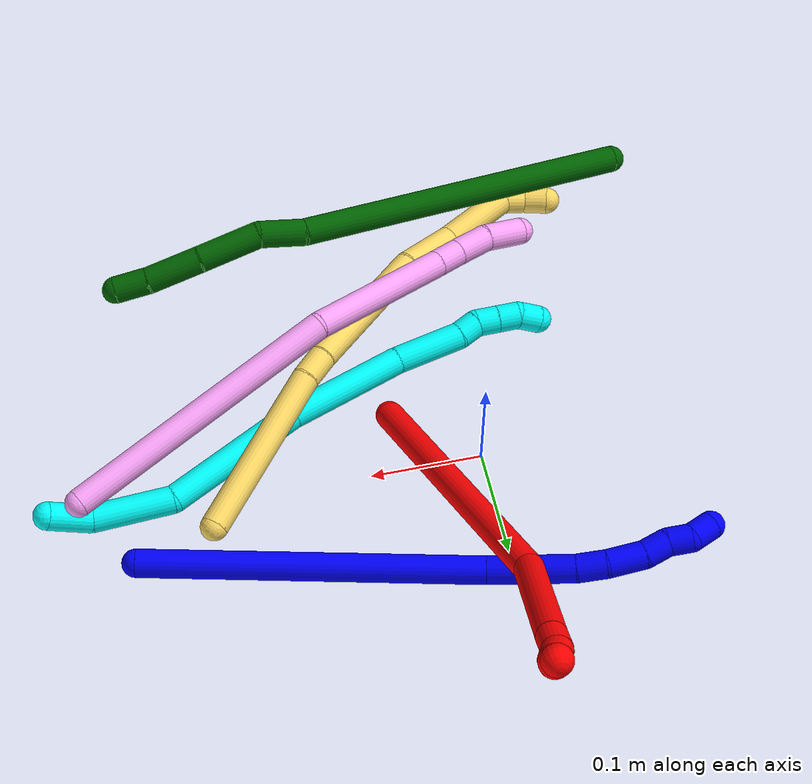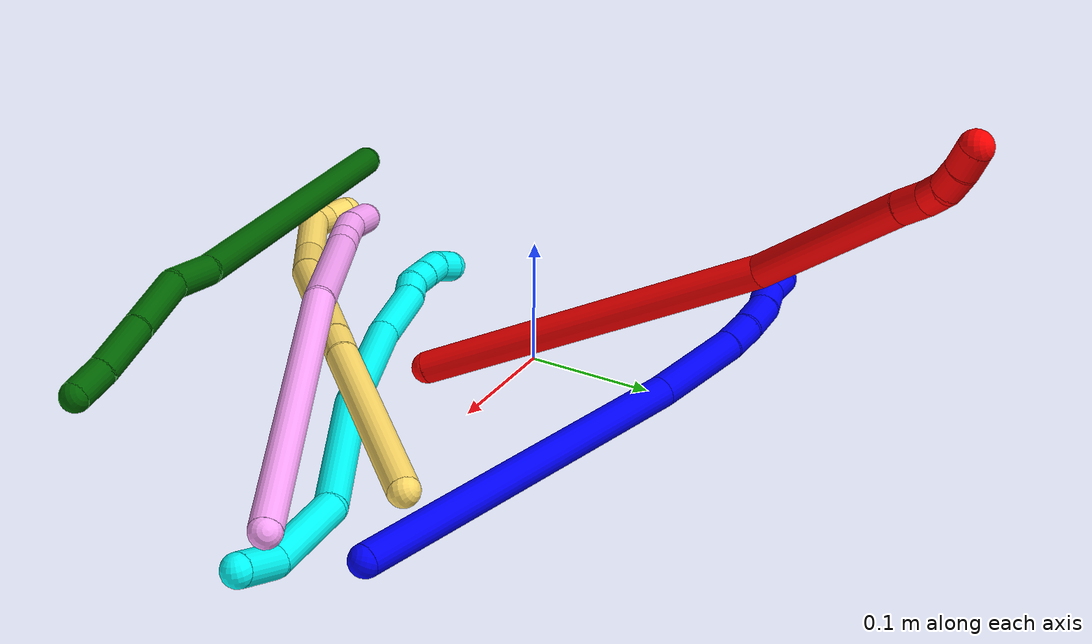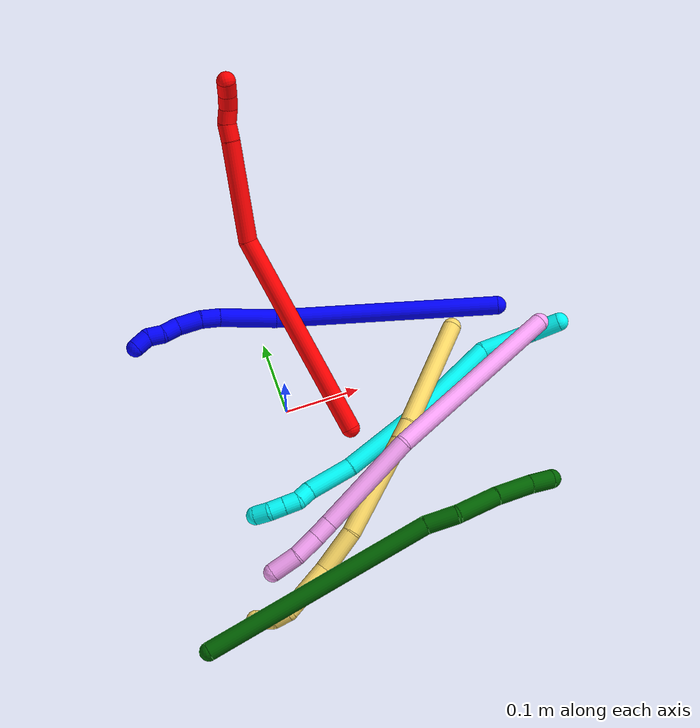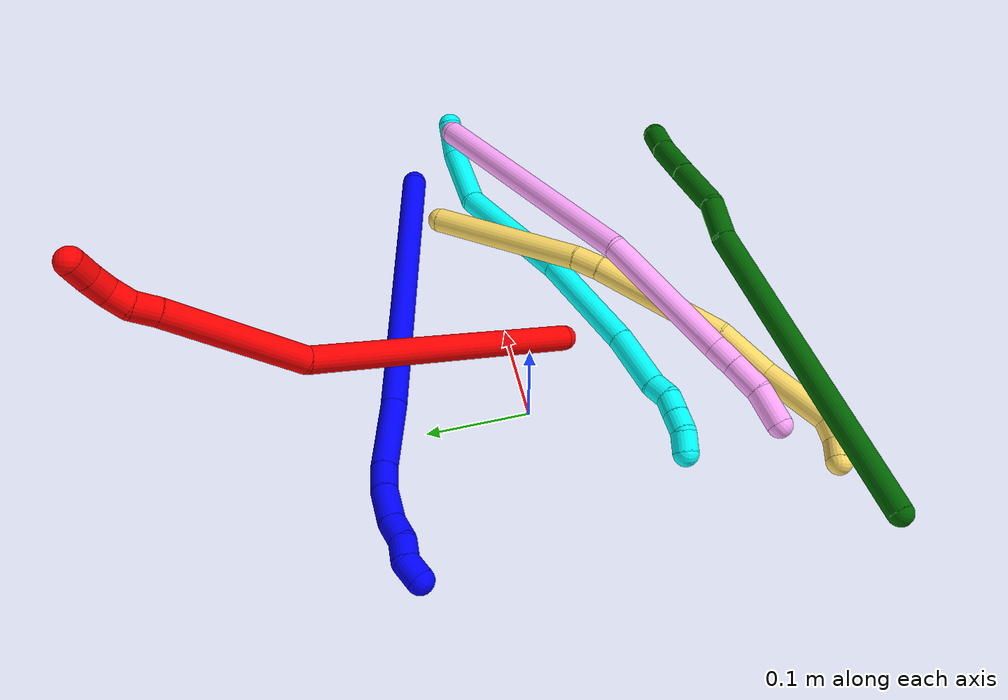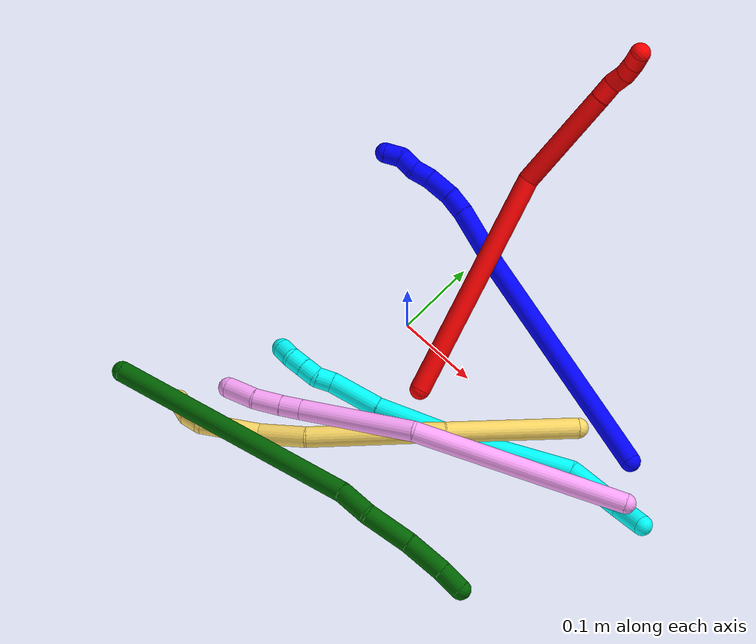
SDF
<sdf version="1.7">
 <world name="default">
  <plugin name="TubeGeneratorPlugin" filename="libtube_generator_plugin.so"/>
  <model name="photoneo_s_sensor">
   <static>1</static>
   <pose>0 0 2 1.57079 1.57079 3.14159</pose>
   <link name="link">
    <inertial><mass>0.1</mass></inertial>
    <sensor name="sensor" type="depth">
     <update_rate>30</update_rate>
     <camera>
      <horizontal_fov>1.22</horizontal_fov>
      <image><width>1920</width><height>1200</height><format>B8G8R8</format></image>
      <clip><near>0.1</near><far>4</far></clip>
      <depth_camera><output>points</output></depth_camera>
     </camera>
     <plugin name="camera_plugin" filename="libgazebo_ros_depth_camera.so">
      <baseline>0.2</baseline>
      <alwaysOn>1</alwaysOn>
      <updateRate>0.0</updateRate>
      <cameraName>camera_ir</cameraName>
      <imageTopicName>/camera/color/image_raw</imageTopicName>
      <cameraInfoTopicName>/camera/color/camera_info</cameraInfoTopicName>
      <depthImageTopicName>/camera/depth/image_raw</depthImageTopicName>
      <depthImageCameraInfoTopicName>/camera/depth/camera_info</depthImageCameraInfoTopicName>
      <pointCloudTopicName>/camera/depth/points</pointCloudTopicName>
      <frameName>fr_optical</frameName>
      <pointCloudCutoff>0.1</pointCloudCutoff>
      <pointCloudCutoffMax>2.0</pointCloudCutoffMax>
      <distortionK1>0</distortionK1>
      <distortionK2>0</distortionK2>
      <distortionK3>0</distortionK3>
      <distortionT1>0</distortionT1>
      <distortionT2>0</distortionT2>
      <CxPrime>0</CxPrime>
      <Cx>0</Cx>
      <Cy>0</Cy>
      <focalLength>0</focalLength>
      <hackBaseline>0</hackBaseline>
     </plugin>
    </sensor>
   </link>
  </model>
  <gravity>0 0 -9.8</gravity>
  <magnetic_field>6e-06 2.3e-05 -4.2e-05</magnetic_field>
  <atmosphere type="adiabatic"/>
  <physics name="default_physics" default="0" type="ode">
   <max_step_size>0.003</max_step_size>
   <real_time_factor>1</real_time_factor>
   <real_time_update_rate>1000</real_time_update_rate>
   <max_contacts>10000</max_contacts>
   <ode>
    <solver>
     <type>quick</type>
     <iters>100</iters>
     <sor>1.3</sor>
     <use_dynamic_moi_rescaling>0</use_dynamic_moi_rescaling>
    </solver>
    <constraints>
     <contact_max_correcting_vel>0</contact_max_correcting_vel>
     <contact_surface_layer>0.001</contact_surface_layer>
     <cfm>0</cfm>
     <erp>0.2</erp>
    </constraints>
   </ode>
  </physics>
  <scene><ambient>0.4 0.4 0.4 1</ambient><background>0.7 0.7 0.7 1</background><shadows>0</shadows></scene>
  <audio><device>default</device></audio>
  <spherical_coordinates>
   <surface_model>EARTH_WGS84</surface_model>
   <latitude_deg>0</latitude_deg>
   <longitude_deg>0</longitude_deg>
   <elevation>0</elevation>
   <heading_deg>0</heading_deg>
  </spherical_coordinates>
  <model name="bin">
   <static>1</static>
   <link name="bottom">
    <collision name="collision-bottom">
     <pose>0 0 -0.01 0 -0 0</pose>
     <geometry><box><size>0.8 0.6 0.02</size></box></geometry>
     <surface>
      <friction><ode><mu>100</mu><mu2>100</mu2></ode></friction>
      <contact><collide_bitmask>65535</collide_bitmask></contact>
     </surface>
    </collision>
   </link>
   <link name="west_wall">
    <collision name="collision-west_wall">
     <pose>-0.41 0 0.1 0 -0 0</pose>
     <geometry><box><size>0.02 0.6 0.2</size></box></geometry>
     <surface>
      <friction><ode><mu>100</mu><mu2>100</mu2></ode></friction>
      <contact><collide_bitmask>65535</collide_bitmask></contact>
     </surface>
    </collision>
   </link>
   <link name="east_wall">
    <collision name="collision-east_wall">
     <pose>0.41 0 0.1 0 -0 0</pose>
     <geometry><box><size>0.02 0.6 0.2</size></box></geometry>
     <surface>
      <friction><ode><mu>100</mu><mu2>100</mu2></ode></friction>
      <contact><collide_bitmask>65535</collide_bitmask></contact>
     </surface>
    </collision>
   </link>
   <link name="south_wall">
    <collision name="collision-south_wall">
     <pose>0 -0.31 0.1 0 -0 0</pose>
     <geometry><box><size>0.8 0.02 0.2</size></box></geometry>
     <surface>
      <friction><ode><mu>100</mu><mu2>100</mu2></ode></friction>
      <contact><collide_bitmask>65535</collide_bitmask></contact>
     </surface>
    </collision>
   </link>
   <link name="north_wall">
    <collision name="collision-north_wall">
     <pose>0 0.31 0.1 0 -0 0</pose>
     <geometry><box><size>0.8 0.02 0.2</size></box></geometry>
     <surface>
      <friction><ode><mu>100</mu><mu2>100</mu2></ode></friction>
      <contact><collide_bitmask>65535</collide_bitmask></contact>
     </surface>
    </collision>
   </link>
  </model>
  <model name="1">
   <static>0</static>
   <link name="1">
    <collision name="collision-cylinder-e_1_1_4">
     <pose>-0.093249 -0.012982 -0.116872 3.03097 -0.670455 -2.82636</pose>
     <geometry><cylinder><radius>0.0125</radius><length>0.300153</length></cylinder></geometry>
     <surface>
      <friction><ode><mu>1.16</mu><mu2>1.16</mu2><slip1>0</slip1><slip2>0</slip2></ode></friction>
      <contact><ode><kp>1e+06</kp><kd>1</kd><max_vel>0</max_vel><min_depth>0.001</min_depth></ode></contact>
     </surface>
    </collision>
    <visual name="visual-cylinder-e_1_1_4">
     <pose>-0.093249 -0.012982 -0.116872 3.03097 -0.670455 -2.82636</pose>
     <geometry><cylinder><radius>0.0125</radius><length>0.300153</length></cylinder></geometry>
     <material><ambient>0 0 1 1</ambient></material>
    </visual>
    <collision name="collision-cylinder-e_2_4_5">
     <pose>-0.212755 -0.025501 -0.26146 -3.12489 -0.758295 3.09967</pose>
     <geometry><cylinder><radius>0.0125</radius><length>0.076363</length></cylinder></geometry>
     <surface>
      <friction><ode><mu>1.16</mu><mu2>1.16</mu2><slip1>0</slip1><slip2>0</slip2></ode></friction>
      <contact><ode><kp>1e+06</kp><kd>1</kd><max_vel>0</max_vel><min_depth>0.001</min_depth></ode></contact>
     </surface>
    </collision>
    <visual name="visual-cylinder-e_2_4_5">
     <pose>-0.212755 -0.025501 -0.26146 -3.12489 -0.758295 3.09967</pose>
     <geometry><cylinder><radius>0.0125</radius><length>0.076363</length></cylinder></geometry>
     <material><ambient>0 0 1 1</ambient></material>
    </visual>
    <collision name="collision-cylinder-e_3_5_6">
     <pose>-0.248749 -0.026116 -0.297613 3.01453 -0.852862 -2.86334</pose>
     <geometry><cylinder><radius>0.0125</radius><length>0.025858</length></cylinder></geometry>
     <surface>
      <friction><ode><mu>1.16</mu><mu2>1.16</mu2><slip1>0</slip1><slip2>0</slip2></ode></friction>
      <contact><ode><kp>1e+06</kp><kd>1</kd><max_vel>0</max_vel><min_depth>0.001</min_depth></ode></contact>
     </surface>
    </collision>
    <visual name="visual-cylinder-e_3_5_6">
     <pose>-0.248749 -0.026116 -0.297613 3.01453 -0.852862 -2.86334</pose>
     <geometry><cylinder><radius>0.0125</radius><length>0.025858</length></cylinder></geometry>
     <material><ambient>0 0 1 1</ambient></material>
    </visual>
    <collision name="collision-cylinder-e_4_6_7">
     <pose>-0.270523 -0.031819 -0.316069 2.70906 -0.828728 -2.21508</pose>
     <geometry><cylinder><radius>0.0125</radius><length>0.032659</length></cylinder></geometry>
     <surface>
      <friction><ode><mu>1.16</mu><mu2>1.16</mu2><slip1>0</slip1><slip2>0</slip2></ode></friction>
      <contact><ode><kp>1e+06</kp><kd>1</kd><max_vel>0</max_vel><min_depth>0.001</min_depth></ode></contact>
     </surface>
    </collision>
    <visual name="visual-cylinder-e_4_6_7">
     <pose>-0.270523 -0.031819 -0.316069 2.70906 -0.828728 -2.21508</pose>
     <geometry><cylinder><radius>0.0125</radius><length>0.032659</length></cylinder></geometry>
     <material><ambient>0 0 1 1</ambient></material>
    </visual>
    <collision name="collision-cylinder-e_5_7_8">
     <pose>-0.291971 -0.04081 -0.330665 2.37983 -0.979128 -1.85264</pose>
     <geometry><cylinder><radius>0.0125</radius><length>0.022679</length></cylinder></geometry>
     <surface>
      <friction><ode><mu>1.16</mu><mu2>1.16</mu2><slip1>0</slip1><slip2>0</slip2></ode></friction>
      <contact><ode><kp>1e+06</kp><kd>1</kd><max_vel>0</max_vel><min_depth>0.001</min_depth></ode></contact>
     </surface>
    </collision>
    <visual name="visual-cylinder-e_5_7_8">
     <pose>-0.291971 -0.04081 -0.330665 2.37983 -0.979128 -1.85264</pose>
     <geometry><cylinder><radius>0.0125</radius><length>0.022679</length></cylinder></geometry>
     <material><ambient>0 0 1 1</ambient></material>
    </visual>
    <collision name="collision-cylinder-e_6_8_9">
     <pose>-0.308998 -0.047205 -0.342048 2.85184 -0.820152 -2.49398</pose>
     <geometry><cylinder><radius>0.0125</radius><length>0.020826</length></cylinder></geometry>
     <surface>
      <friction><ode><mu>1.16</mu><mu2>1.16</mu2><slip1>0</slip1><slip2>0</slip2></ode></friction>
      <contact><ode><kp>1e+06</kp><kd>1</kd><max_vel>0</max_vel><min_depth>0.001</min_depth></ode></contact>
     </surface>
    </collision>
    <visual name="visual-cylinder-e_6_8_9">
     <pose>-0.308998 -0.047205 -0.342048 2.85184 -0.820152 -2.49398</pose>
     <geometry><cylinder><radius>0.0125</radius><length>0.020826</length></cylinder></geometry>
     <material><ambient>0 0 1 1</ambient></material>
    </visual>
    <collision name="collision-cylinder-e_7_9_2">
     <pose>-0.324174 -0.055791 -0.352727 2.1042 -0.781924 -1.25076</pose>
     <geometry><cylinder><radius>0.0125</radius><length>0.021462</length></cylinder></geometry>
     <surface>
      <friction><ode><mu>1.16</mu><mu2>1.16</mu2><slip1>0</slip1><slip2>0</slip2></ode></friction>
      <contact><ode><kp>1e+06</kp><kd>1</kd><max_vel>0</max_vel><min_depth>0.001</min_depth></ode></contact>
     </surface>
    </collision>
    <visual name="visual-cylinder-e_7_9_2">
     <pose>-0.324174 -0.055791 -0.352727 2.1042 -0.781924 -1.25076</pose>
     <geometry><cylinder><radius>0.0125</radius><length>0.021462</length></cylinder></geometry>
     <material><ambient>0 0 1 1</ambient></material>
    </visual>
    <collision name="collision-sphere-2">
     <pose>-0.331735 -0.062347 -0.356598 0 -0 0</pose>
     <geometry><sphere><radius>0.0125</radius></sphere></geometry>
     <surface>
      <friction><ode><mu>1.16</mu><mu2>1.16</mu2><slip1>0</slip1><slip2>0</slip2></ode></friction>
      <contact><ode><kp>1e+06</kp><kd>1</kd><max_vel>0</max_vel><min_depth>0.001</min_depth></ode></contact>
     </surface>
    </collision>
    <visual name="visual-sphere-2">
     <pose>-0.331735 -0.062347 -0.356598 0 -0 0</pose>
     <geometry><sphere><radius>0.0125</radius></sphere></geometry>
     <material><ambient>0 0 1 1</ambient></material>
    </visual>
    <collision name="collision-sphere-9">
     <pose>-0.316612 -0.049235 -0.348855 0 -0 0</pose>
     <geometry><sphere><radius>0.0125</radius></sphere></geometry>
     <surface>
      <friction><ode><mu>1.16</mu><mu2>1.16</mu2><slip1>0</slip1><slip2>0</slip2></ode></friction>
      <contact><ode><kp>1e+06</kp><kd>1</kd><max_vel>0</max_vel><min_depth>0.001</min_depth></ode></contact>
     </surface>
    </collision>
    <visual name="visual-sphere-9">
     <pose>-0.316612 -0.049235 -0.348855 0 -0 0</pose>
     <geometry><sphere><radius>0.0125</radius></sphere></geometry>
     <material><ambient>0 0 1 1</ambient></material>
    </visual>
    <collision name="collision-sphere-4">
     <pose>-0.186498 -0.025964 -0.233744 0 -0 0</pose>
     <geometry><sphere><radius>0.0125</radius></sphere></geometry>
     <surface>
      <friction><ode><mu>1.16</mu><mu2>1.16</mu2><slip1>0</slip1><slip2>0</slip2></ode></friction>
      <contact><ode><kp>1e+06</kp><kd>1</kd><max_vel>0</max_vel><min_depth>0.001</min_depth></ode></contact>
     </surface>
    </collision>
    <visual name="visual-sphere-4">
     <pose>-0.186498 -0.025964 -0.233744 0 -0 0</pose>
     <geometry><sphere><radius>0.0125</radius></sphere></geometry>
     <material><ambient>0 0 1 1</ambient></material>
    </visual>
    <collision name="collision-sphere-1">
     <geometry><sphere><radius>0.0125</radius></sphere></geometry>
     <surface>
      <friction><ode><mu>1.16</mu><mu2>1.16</mu2><slip1>0</slip1><slip2>0</slip2></ode></friction>
      <contact><ode><kp>1e+06</kp><kd>1</kd><max_vel>0</max_vel><min_depth>0.001</min_depth></ode></contact>
     </surface>
    </collision>
    <visual name="visual-sphere-1">
     <geometry><sphere><radius>0.0125</radius></sphere></geometry>
     <material><ambient>0 0 1 1</ambient></material>
    </visual>
    <collision name="collision-sphere-8">
     <pose>-0.301383 -0.045176 -0.335242 0 -0 0</pose>
     <geometry><sphere><radius>0.0125</radius></sphere></geometry>
     <surface>
      <friction><ode><mu>1.16</mu><mu2>1.16</mu2><slip1>0</slip1><slip2>0</slip2></ode></friction>
      <contact><ode><kp>1e+06</kp><kd>1</kd><max_vel>0</max_vel><min_depth>0.001</min_depth></ode></contact>
     </surface>
    </collision>
    <visual name="visual-sphere-8">
     <pose>-0.301383 -0.045176 -0.335242 0 -0 0</pose>
     <geometry><sphere><radius>0.0125</radius></sphere></geometry>
     <material><ambient>0 0 1 1</ambient></material>
    </visual>
    <collision name="collision-sphere-5">
     <pose>-0.239011 -0.025038 -0.289176 0 -0 0</pose>
     <geometry><sphere><radius>0.0125</radius></sphere></geometry>
     <surface>
      <friction><ode><mu>1.16</mu><mu2>1.16</mu2><slip1>0</slip1><slip2>0</slip2></ode></friction>
      <contact><ode><kp>1e+06</kp><kd>1</kd><max_vel>0</max_vel><min_depth>0.001</min_depth></ode></contact>
     </surface>
    </collision>
    <visual name="visual-sphere-5">
     <pose>-0.239011 -0.025038 -0.289176 0 -0 0</pose>
     <geometry><sphere><radius>0.0125</radius></sphere></geometry>
     <material><ambient>0 0 1 1</ambient></material>
    </visual>
    <collision name="collision-sphere-6">
     <pose>-0.258487 -0.027194 -0.30605 0 -0 0</pose>
     <geometry><sphere><radius>0.0125</radius></sphere></geometry>
     <surface>
      <friction><ode><mu>1.16</mu><mu2>1.16</mu2><slip1>0</slip1><slip2>0</slip2></ode></friction>
      <contact><ode><kp>1e+06</kp><kd>1</kd><max_vel>0</max_vel><min_depth>0.001</min_depth></ode></contact>
     </surface>
    </collision>
    <visual name="visual-sphere-6">
     <pose>-0.258487 -0.027194 -0.30605 0 -0 0</pose>
     <geometry><sphere><radius>0.0125</radius></sphere></geometry>
     <material><ambient>0 0 1 1</ambient></material>
    </visual>
    <collision name="collision-sphere-7">
     <pose>-0.282559 -0.036445 -0.326088 0 -0 0</pose>
     <geometry><sphere><radius>0.0125</radius></sphere></geometry>
     <surface>
      <friction><ode><mu>1.16</mu><mu2>1.16</mu2><slip1>0</slip1><slip2>0</slip2></ode></friction>
      <contact><ode><kp>1e+06</kp><kd>1</kd><max_vel>0</max_vel><min_depth>0.001</min_depth></ode></contact>
     </surface>
    </collision>
    <visual name="visual-sphere-7">
     <pose>-0.282559 -0.036445 -0.326088 0 -0 0</pose>
     <geometry><sphere><radius>0.0125</radius></sphere></geometry>
     <material><ambient>0 0 1 1</ambient></material>
    </visual>
    <inertial>
     <pose>-0.159034 -0.021329 -0.190513 0 -0 0</pose>
     <mass>0.5</mass>
     <inertia>
      <ixx>-0.002301</ixx>
      <ixy>0</ixy>
      <ixz>0</ixz>
      <iyy>0.001678</iyy>
      <iyz>0</iyz>
      <izz>0.001615</izz>
     </inertia>
    </inertial>
   </link>
   <pose>0.317071 0.051595 0.012116 0.922068 0.744205 0.355994</pose>
  </model>
  <model name="2">
   <static>0</static>
   <link name="2">
    <collision name="collision-cylinder-e_1_1_4">
     <pose>0.000659 0.038646 0.135613 -0.277617 0.004675 -0.000653</pose>
     <geometry><cylinder><radius>0.0125</radius><length>0.282027</length></cylinder></geometry>
     <surface>
      <friction><ode><mu>1.16</mu><mu2>1.16</mu2><slip1>0</slip1><slip2>0</slip2></ode></friction>
      <contact><ode><kp>1e+06</kp><kd>1</kd><max_vel>0</max_vel><min_depth>0.001</min_depth></ode></contact>
     </surface>
    </collision>
    <visual name="visual-cylinder-e_1_1_4">
     <pose>0.000659 0.038646 0.135613 -0.277617 0.004675 -0.000653</pose>
     <geometry><cylinder><radius>0.0125</radius><length>0.282027</length></cylinder></geometry>
     <material><ambient>1 0 0 1</ambient></material>
    </visual>
    <collision name="collision-cylinder-e_2_4_5">
     <pose>-0.020253 0.08428 0.33444 -0.110081 -0.327 0.018178</pose>
     <geometry><cylinder><radius>0.0125</radius><length>0.134315</length></cylinder></geometry>
     <surface>
      <friction><ode><mu>1.16</mu><mu2>1.16</mu2><slip1>0</slip1><slip2>0</slip2></ode></friction>
      <contact><ode><kp>1e+06</kp><kd>1</kd><max_vel>0</max_vel><min_depth>0.001</min_depth></ode></contact>
     </surface>
    </collision>
    <visual name="visual-cylinder-e_2_4_5">
     <pose>-0.020253 0.08428 0.33444 -0.110081 -0.327 0.018178</pose>
     <geometry><cylinder><radius>0.0125</radius><length>0.134315</length></cylinder></geometry>
     <material><ambient>1 0 0 1</ambient></material>
    </visual>
    <collision name="collision-cylinder-e_3_5_6">
     <pose>-0.044558 0.092448 0.408677 -0.106803 -0.241829 0.012989</pose>
     <geometry><cylinder><radius>0.0125</radius><length>0.022838</length></cylinder></geometry>
     <surface>
      <friction><ode><mu>1.16</mu><mu2>1.16</mu2><slip1>0</slip1><slip2>0</slip2></ode></friction>
      <contact><ode><kp>1e+06</kp><kd>1</kd><max_vel>0</max_vel><min_depth>0.001</min_depth></ode></contact>
     </surface>
    </collision>
    <visual name="visual-cylinder-e_3_5_6">
     <pose>-0.044558 0.092448 0.408677 -0.106803 -0.241829 0.012989</pose>
     <geometry><cylinder><radius>0.0125</radius><length>0.022838</length></cylinder></geometry>
     <material><ambient>1 0 0 1</ambient></material>
    </visual>
    <collision name="collision-cylinder-e_4_6_7">
     <pose>-0.052404 0.093011 0.428524 0.070083 -0.524013 -0.018801</pose>
     <geometry><cylinder><radius>0.0125</radius><length>0.020431</length></cylinder></geometry>
     <surface>
      <friction><ode><mu>1.16</mu><mu2>1.16</mu2><slip1>0</slip1><slip2>0</slip2></ode></friction>
      <contact><ode><kp>1e+06</kp><kd>1</kd><max_vel>0</max_vel><min_depth>0.001</min_depth></ode></contact>
     </surface>
    </collision>
    <visual name="visual-cylinder-e_4_6_7">
     <pose>-0.052404 0.093011 0.428524 0.070083 -0.524013 -0.018801</pose>
     <geometry><cylinder><radius>0.0125</radius><length>0.020431</length></cylinder></geometry>
     <material><ambient>1 0 0 1</ambient></material>
    </visual>
    <collision name="collision-cylinder-e_5_7_8">
     <pose>-0.063791 0.09449 0.444951 -0.269257 -0.67196 0.094532</pose>
     <geometry><cylinder><radius>0.0125</radius><length>0.02016</length></cylinder></geometry>
     <surface>
      <friction><ode><mu>1.16</mu><mu2>1.16</mu2><slip1>0</slip1><slip2>0</slip2></ode></friction>
      <contact><ode><kp>1e+06</kp><kd>1</kd><max_vel>0</max_vel><min_depth>0.001</min_depth></ode></contact>
     </surface>
    </collision>
    <visual name="visual-cylinder-e_5_7_8">
     <pose>-0.063791 0.09449 0.444951 -0.269257 -0.67196 0.094532</pose>
     <geometry><cylinder><radius>0.0125</radius><length>0.02016</length></cylinder></geometry>
     <material><ambient>1 0 0 1</ambient></material>
    </visual>
    <collision name="collision-cylinder-e_6_8_2">
     <pose>-0.0768 0.099813 0.459379 -0.441508 -0.728541 0.170714</pose>
     <geometry><cylinder><radius>0.0125</radius><length>0.020229</length></cylinder></geometry>
     <surface>
      <friction><ode><mu>1.16</mu><mu2>1.16</mu2><slip1>0</slip1><slip2>0</slip2></ode></friction>
      <contact><ode><kp>1e+06</kp><kd>1</kd><max_vel>0</max_vel><min_depth>0.001</min_depth></ode></contact>
     </surface>
    </collision>
    <visual name="visual-cylinder-e_6_8_2">
     <pose>-0.0768 0.099813 0.459379 -0.441508 -0.728541 0.170714</pose>
     <geometry><cylinder><radius>0.0125</radius><length>0.020229</length></cylinder></geometry>
     <material><ambient>1 0 0 1</ambient></material>
    </visual>
    <collision name="collision-sphere-2">
     <pose>-0.083534 0.103038 0.466202 0 -0 0</pose>
     <geometry><sphere><radius>0.0125</radius></sphere></geometry>
     <surface>
      <friction><ode><mu>1.16</mu><mu2>1.16</mu2><slip1>0</slip1><slip2>0</slip2></ode></friction>
      <contact><ode><kp>1e+06</kp><kd>1</kd><max_vel>0</max_vel><min_depth>0.001</min_depth></ode></contact>
     </surface>
    </collision>
    <visual name="visual-sphere-2">
     <pose>-0.083534 0.103038 0.466202 0 -0 0</pose>
     <geometry><sphere><radius>0.0125</radius></sphere></geometry>
     <material><ambient>1 0 0 1</ambient></material>
    </visual>
    <collision name="collision-sphere-4">
     <pose>0.001319 0.077293 0.271226 0 -0 0</pose>
     <geometry><sphere><radius>0.0125</radius></sphere></geometry>
     <surface>
      <friction><ode><mu>1.16</mu><mu2>1.16</mu2><slip1>0</slip1><slip2>0</slip2></ode></friction>
      <contact><ode><kp>1e+06</kp><kd>1</kd><max_vel>0</max_vel><min_depth>0.001</min_depth></ode></contact>
     </surface>
    </collision>
    <visual name="visual-sphere-4">
     <pose>0.001319 0.077293 0.271226 0 -0 0</pose>
     <geometry><sphere><radius>0.0125</radius></sphere></geometry>
     <material><ambient>1 0 0 1</ambient></material>
    </visual>
    <collision name="collision-sphere-1">
     <geometry><sphere><radius>0.0125</radius></sphere></geometry>
     <surface>
      <friction><ode><mu>1.16</mu><mu2>1.16</mu2><slip1>0</slip1><slip2>0</slip2></ode></friction>
      <contact><ode><kp>1e+06</kp><kd>1</kd><max_vel>0</max_vel><min_depth>0.001</min_depth></ode></contact>
     </surface>
    </collision>
    <visual name="visual-sphere-1">
     <geometry><sphere><radius>0.0125</radius></sphere></geometry>
     <material><ambient>1 0 0 1</ambient></material>
    </visual>
    <collision name="collision-sphere-8">
     <pose>-0.070066 0.096589 0.452555 0 -0 0</pose>
     <geometry><sphere><radius>0.0125</radius></sphere></geometry>
     <surface>
      <friction><ode><mu>1.16</mu><mu2>1.16</mu2><slip1>0</slip1><slip2>0</slip2></ode></friction>
      <contact><ode><kp>1e+06</kp><kd>1</kd><max_vel>0</max_vel><min_depth>0.001</min_depth></ode></contact>
     </surface>
    </collision>
    <visual name="visual-sphere-8">
     <pose>-0.070066 0.096589 0.452555 0 -0 0</pose>
     <geometry><sphere><radius>0.0125</radius></sphere></geometry>
     <material><ambient>1 0 0 1</ambient></material>
    </visual>
    <collision name="collision-sphere-5">
     <pose>-0.041824 0.091267 0.397654 0 -0 0</pose>
     <geometry><sphere><radius>0.0125</radius></sphere></geometry>
     <surface>
      <friction><ode><mu>1.16</mu><mu2>1.16</mu2><slip1>0</slip1><slip2>0</slip2></ode></friction>
      <contact><ode><kp>1e+06</kp><kd>1</kd><max_vel>0</max_vel><min_depth>0.001</min_depth></ode></contact>
     </surface>
    </collision>
    <visual name="visual-sphere-5">
     <pose>-0.041824 0.091267 0.397654 0 -0 0</pose>
     <geometry><sphere><radius>0.0125</radius></sphere></geometry>
     <material><ambient>1 0 0 1</ambient></material>
    </visual>
    <collision name="collision-sphere-6">
     <pose>-0.047293 0.09363 0.419701 0 -0 0</pose>
     <geometry><sphere><radius>0.0125</radius></sphere></geometry>
     <surface>
      <friction><ode><mu>1.16</mu><mu2>1.16</mu2><slip1>0</slip1><slip2>0</slip2></ode></friction>
      <contact><ode><kp>1e+06</kp><kd>1</kd><max_vel>0</max_vel><min_depth>0.001</min_depth></ode></contact>
     </surface>
    </collision>
    <visual name="visual-sphere-6">
     <pose>-0.047293 0.09363 0.419701 0 -0 0</pose>
     <geometry><sphere><radius>0.0125</radius></sphere></geometry>
     <material><ambient>1 0 0 1</ambient></material>
    </visual>
    <collision name="collision-sphere-7">
     <pose>-0.057516 0.092392 0.437347 0 -0 0</pose>
     <geometry><sphere><radius>0.0125</radius></sphere></geometry>
     <surface>
      <friction><ode><mu>1.16</mu><mu2>1.16</mu2><slip1>0</slip1><slip2>0</slip2></ode></friction>
      <contact><ode><kp>1e+06</kp><kd>1</kd><max_vel>0</max_vel><min_depth>0.001</min_depth></ode></contact>
     </surface>
    </collision>
    <visual name="visual-sphere-7">
     <pose>-0.057516 0.092392 0.437347 0 -0 0</pose>
     <geometry><sphere><radius>0.0125</radius></sphere></geometry>
     <material><ambient>1 0 0 1</ambient></material>
    </visual>
    <inertial>
     <pose>-0.014924 0.06031 0.239036 0 -0 0</pose>
     <mass>0.5</mass>
     <inertia>
      <ixx>0.002078</ixx>
      <ixy>0</ixy>
      <ixz>0</ixz>
      <iyy>0.002031</iyy>
      <iyz>0</iyz>
      <izz>-0.00044</izz>
     </inertia>
    </inertial>
   </link>
   <pose>0.072097 -0.053338 0.011497 1.00225 0.949317 2.62866</pose>
  </model>
  <model name="3">
   <static>0</static>
   <link name="3">
    <collision name="collision-cylinder-e_1_1_4">
     <pose>-0.018708 0.000152 -0.006574 -3.11844 -1.2328 3.10892</pose>
     <geometry><cylinder><radius>0.0125</radius><length>0.03966</length></cylinder></geometry>
     <surface>
      <friction><ode><mu>1.16</mu><mu2>1.16</mu2><slip1>0</slip1><slip2>0</slip2></ode></friction>
      <contact><ode><kp>1e+06</kp><kd>1</kd><max_vel>0</max_vel><min_depth>0.001</min_depth></ode></contact>
     </surface>
    </collision>
    <visual name="visual-cylinder-e_1_1_4">
     <pose>-0.018708 0.000152 -0.006574 -3.11844 -1.2328 3.10892</pose>
     <geometry><cylinder><radius>0.0125</radius><length>0.03966</length></cylinder></geometry>
     <material><ambient>0.003922 1 0.996078 1</ambient></material>
    </visual>
    <collision name="collision-cylinder-e_2_4_5">
     <pose>-0.073826 -0.000347 -0.011537 0.384258 -1.52311 -0.366765</pose>
     <geometry><cylinder><radius>0.0125</radius><length>0.072902</length></cylinder></geometry>
     <surface>
      <friction><ode><mu>1.16</mu><mu2>1.16</mu2><slip1>0</slip1><slip2>0</slip2></ode></friction>
      <contact><ode><kp>1e+06</kp><kd>1</kd><max_vel>0</max_vel><min_depth>0.001</min_depth></ode></contact>
     </surface>
    </collision>
    <visual name="visual-cylinder-e_2_4_5">
     <pose>-0.073826 -0.000347 -0.011537 0.384258 -1.52311 -0.366765</pose>
     <geometry><cylinder><radius>0.0125</radius><length>0.072902</length></cylinder></geometry>
     <material><ambient>0.003922 1 0.996078 1</ambient></material>
    </visual>
    <collision name="collision-cylinder-e_3_5_6">
     <pose>-0.169569 -0.028057 0.001071 1.18478 -1.11335 -0.793285</pose>
     <geometry><cylinder><radius>0.0125</radius><length>0.132266</length></cylinder></geometry>
     <surface>
      <friction><ode><mu>1.16</mu><mu2>1.16</mu2><slip1>0</slip1><slip2>0</slip2></ode></friction>
      <contact><ode><kp>1e+06</kp><kd>1</kd><max_vel>0</max_vel><min_depth>0.001</min_depth></ode></contact>
     </surface>
    </collision>
    <visual name="visual-cylinder-e_3_5_6">
     <pose>-0.169569 -0.028057 0.001071 1.18478 -1.11335 -0.793285</pose>
     <geometry><cylinder><radius>0.0125</radius><length>0.132266</length></cylinder></geometry>
     <material><ambient>0.003922 1 0.996078 1</ambient></material>
    </visual>
    <collision name="collision-cylinder-e_4_6_7">
     <pose>-0.281697 -0.073085 0.016896 1.30831 -1.23197 -0.994564</pose>
     <geometry><cylinder><radius>0.0125</radius><length>0.111955</length></cylinder></geometry>
     <surface>
      <friction><ode><mu>1.16</mu><mu2>1.16</mu2><slip1>0</slip1><slip2>0</slip2></ode></friction>
      <contact><ode><kp>1e+06</kp><kd>1</kd><max_vel>0</max_vel><min_depth>0.001</min_depth></ode></contact>
     </surface>
    </collision>
    <visual name="visual-cylinder-e_4_6_7">
     <pose>-0.281697 -0.073085 0.016896 1.30831 -1.23197 -0.994564</pose>
     <geometry><cylinder><radius>0.0125</radius><length>0.111955</length></cylinder></geometry>
     <material><ambient>0.003922 1 0.996078 1</ambient></material>
    </visual>
    <collision name="collision-cylinder-e_5_7_8">
     <pose>-0.365289 -0.096813 0.024642 1.1018 -1.36414 -0.92554</pose>
     <geometry><cylinder><radius>0.0125</radius><length>0.062933</length></cylinder></geometry>
     <surface>
      <friction><ode><mu>1.16</mu><mu2>1.16</mu2><slip1>0</slip1><slip2>0</slip2></ode></friction>
      <contact><ode><kp>1e+06</kp><kd>1</kd><max_vel>0</max_vel><min_depth>0.001</min_depth></ode></contact>
     </surface>
    </collision>
    <visual name="visual-cylinder-e_5_7_8">
     <pose>-0.365289 -0.096813 0.024642 1.1018 -1.36414 -0.92554</pose>
     <geometry><cylinder><radius>0.0125</radius><length>0.062933</length></cylinder></geometry>
     <material><ambient>0.003922 1 0.996078 1</ambient></material>
    </visual>
    <collision name="collision-cylinder-e_6_8_9">
     <pose>-0.405123 -0.106331 0.029843 1.02499 -1.11792 -0.676791</pose>
     <geometry><cylinder><radius>0.0125</radius><length>0.020101</length></cylinder></geometry>
     <surface>
      <friction><ode><mu>1.16</mu><mu2>1.16</mu2><slip1>0</slip1><slip2>0</slip2></ode></friction>
      <contact><ode><kp>1e+06</kp><kd>1</kd><max_vel>0</max_vel><min_depth>0.001</min_depth></ode></contact>
     </surface>
    </collision>
    <visual name="visual-cylinder-e_6_8_9">
     <pose>-0.405123 -0.106331 0.029843 1.02499 -1.11792 -0.676791</pose>
     <geometry><cylinder><radius>0.0125</radius><length>0.020101</length></cylinder></geometry>
     <material><ambient>0.003922 1 0.996078 1</ambient></material>
    </visual>
    <collision name="collision-cylinder-e_7_9_10">
     <pose>-0.424209 -0.11025 0.032123 1.59013 -1.55485 -1.57418</pose>
     <geometry><cylinder><radius>0.0125</radius><length>0.020101</length></cylinder></geometry>
     <surface>
      <friction><ode><mu>1.16</mu><mu2>1.16</mu2><slip1>0</slip1><slip2>0</slip2></ode></friction>
      <contact><ode><kp>1e+06</kp><kd>1</kd><max_vel>0</max_vel><min_depth>0.001</min_depth></ode></contact>
     </surface>
    </collision>
    <visual name="visual-cylinder-e_7_9_10">
     <pose>-0.424209 -0.11025 0.032123 1.59013 -1.55485 -1.57418</pose>
     <geometry><cylinder><radius>0.0125</radius><length>0.020101</length></cylinder></geometry>
     <material><ambient>0.003922 1 0.996078 1</ambient></material>
    </visual>
    <collision name="collision-cylinder-e_8_10_11">
     <pose>-0.444262 -0.110638 0.032077 1.75364 -1.54766 -1.73085</pose>
     <geometry><cylinder><radius>0.0125</radius><length>0.020013</length></cylinder></geometry>
     <surface>
      <friction><ode><mu>1.16</mu><mu2>1.16</mu2><slip1>0</slip1><slip2>0</slip2></ode></friction>
      <contact><ode><kp>1e+06</kp><kd>1</kd><max_vel>0</max_vel><min_depth>0.001</min_depth></ode></contact>
     </surface>
    </collision>
    <visual name="visual-cylinder-e_8_10_11">
     <pose>-0.444262 -0.110638 0.032077 1.75364 -1.54766 -1.73085</pose>
     <geometry><cylinder><radius>0.0125</radius><length>0.020013</length></cylinder></geometry>
     <material><ambient>0.003922 1 0.996078 1</ambient></material>
    </visual>
    <collision name="collision-cylinder-e_9_11_2">
     <pose>-0.463527 -0.109944 0.028283 -2.9007 -1.17554 2.78224</pose>
     <geometry><cylinder><radius>0.0125</radius><length>0.020069</length></cylinder></geometry>
     <surface>
      <friction><ode><mu>1.16</mu><mu2>1.16</mu2><slip1>0</slip1><slip2>0</slip2></ode></friction>
      <contact><ode><kp>1e+06</kp><kd>1</kd><max_vel>0</max_vel><min_depth>0.001</min_depth></ode></contact>
     </surface>
    </collision>
    <visual name="visual-cylinder-e_9_11_2">
     <pose>-0.463527 -0.109944 0.028283 -2.9007 -1.17554 2.78224</pose>
     <geometry><cylinder><radius>0.0125</radius><length>0.020069</length></cylinder></geometry>
     <material><ambient>0.003922 1 0.996078 1</ambient></material>
    </visual>
    <collision name="collision-sphere-2">
     <pose>-0.472788 -0.109022 0.024531 0 -0 0</pose>
     <geometry><sphere><radius>0.0125</radius></sphere></geometry>
     <surface>
      <friction><ode><mu>1.16</mu><mu2>1.16</mu2><slip1>0</slip1><slip2>0</slip2></ode></friction>
      <contact><ode><kp>1e+06</kp><kd>1</kd><max_vel>0</max_vel><min_depth>0.001</min_depth></ode></contact>
     </surface>
    </collision>
    <visual name="visual-sphere-2">
     <pose>-0.472788 -0.109022 0.024531 0 -0 0</pose>
     <geometry><sphere><radius>0.0125</radius></sphere></geometry>
     <material><ambient>0.003922 1 0.996078 1</ambient></material>
    </visual>
    <collision name="collision-sphere-11">
     <pose>-0.454266 -0.110866 0.032035 0 -0 0</pose>
     <geometry><sphere><radius>0.0125</radius></sphere></geometry>
     <surface>
      <friction><ode><mu>1.16</mu><mu2>1.16</mu2><slip1>0</slip1><slip2>0</slip2></ode></friction>
      <contact><ode><kp>1e+06</kp><kd>1</kd><max_vel>0</max_vel><min_depth>0.001</min_depth></ode></contact>
     </surface>
    </collision>
    <visual name="visual-sphere-11">
     <pose>-0.454266 -0.110866 0.032035 0 -0 0</pose>
     <geometry><sphere><radius>0.0125</radius></sphere></geometry>
     <material><ambient>0.003922 1 0.996078 1</ambient></material>
    </visual>
    <collision name="collision-sphere-10">
     <pose>-0.434259 -0.110411 0.03212 0 -0 0</pose>
     <geometry><sphere><radius>0.0125</radius></sphere></geometry>
     <surface>
      <friction><ode><mu>1.16</mu><mu2>1.16</mu2><slip1>0</slip1><slip2>0</slip2></ode></friction>
      <contact><ode><kp>1e+06</kp><kd>1</kd><max_vel>0</max_vel><min_depth>0.001</min_depth></ode></contact>
     </surface>
    </collision>
    <visual name="visual-sphere-10">
     <pose>-0.434259 -0.110411 0.03212 0 -0 0</pose>
     <geometry><sphere><radius>0.0125</radius></sphere></geometry>
     <material><ambient>0.003922 1 0.996078 1</ambient></material>
    </visual>
    <collision name="collision-sphere-9">
     <pose>-0.41416 -0.11009 0.032126 0 -0 0</pose>
     <geometry><sphere><radius>0.0125</radius></sphere></geometry>
     <surface>
      <friction><ode><mu>1.16</mu><mu2>1.16</mu2><slip1>0</slip1><slip2>0</slip2></ode></friction>
      <contact><ode><kp>1e+06</kp><kd>1</kd><max_vel>0</max_vel><min_depth>0.001</min_depth></ode></contact>
     </surface>
    </collision>
    <visual name="visual-sphere-9">
     <pose>-0.41416 -0.11009 0.032126 0 -0 0</pose>
     <geometry><sphere><radius>0.0125</radius></sphere></geometry>
     <material><ambient>0.003922 1 0.996078 1</ambient></material>
    </visual>
    <collision name="collision-sphere-4">
     <pose>-0.037416 0.000304 -0.013148 0 -0 0</pose>
     <geometry><sphere><radius>0.0125</radius></sphere></geometry>
     <surface>
      <friction><ode><mu>1.16</mu><mu2>1.16</mu2><slip1>0</slip1><slip2>0</slip2></ode></friction>
      <contact><ode><kp>1e+06</kp><kd>1</kd><max_vel>0</max_vel><min_depth>0.001</min_depth></ode></contact>
     </surface>
    </collision>
    <visual name="visual-sphere-4">
     <pose>-0.037416 0.000304 -0.013148 0 -0 0</pose>
     <geometry><sphere><radius>0.0125</radius></sphere></geometry>
     <material><ambient>0.003922 1 0.996078 1</ambient></material>
    </visual>
    <collision name="collision-sphere-1">
     <geometry><sphere><radius>0.0125</radius></sphere></geometry>
     <surface>
      <friction><ode><mu>1.16</mu><mu2>1.16</mu2><slip1>0</slip1><slip2>0</slip2></ode></friction>
      <contact><ode><kp>1e+06</kp><kd>1</kd><max_vel>0</max_vel><min_depth>0.001</min_depth></ode></contact>
     </surface>
    </collision>
    <visual name="visual-sphere-1">
     <geometry><sphere><radius>0.0125</radius></sphere></geometry>
     <material><ambient>0.003922 1 0.996078 1</ambient></material>
    </visual>
    <collision name="collision-sphere-8">
     <pose>-0.396085 -0.102573 0.02756 0 -0 0</pose>
     <geometry><sphere><radius>0.0125</radius></sphere></geometry>
     <surface>
      <friction><ode><mu>1.16</mu><mu2>1.16</mu2><slip1>0</slip1><slip2>0</slip2></ode></friction>
      <contact><ode><kp>1e+06</kp><kd>1</kd><max_vel>0</max_vel><min_depth>0.001</min_depth></ode></contact>
     </surface>
    </collision>
    <visual name="visual-sphere-8">
     <pose>-0.396085 -0.102573 0.02756 0 -0 0</pose>
     <geometry><sphere><radius>0.0125</radius></sphere></geometry>
     <material><ambient>0.003922 1 0.996078 1</ambient></material>
    </visual>
    <collision name="collision-sphere-5">
     <pose>-0.110236 -0.000998 -0.009926 0 -0 0</pose>
     <geometry><sphere><radius>0.0125</radius></sphere></geometry>
     <surface>
      <friction><ode><mu>1.16</mu><mu2>1.16</mu2><slip1>0</slip1><slip2>0</slip2></ode></friction>
      <contact><ode><kp>1e+06</kp><kd>1</kd><max_vel>0</max_vel><min_depth>0.001</min_depth></ode></contact>
     </surface>
    </collision>
    <visual name="visual-sphere-5">
     <pose>-0.110236 -0.000998 -0.009926 0 -0 0</pose>
     <geometry><sphere><radius>0.0125</radius></sphere></geometry>
     <material><ambient>0.003922 1 0.996078 1</ambient></material>
    </visual>
    <collision name="collision-sphere-6">
     <pose>-0.228902 -0.055117 0.012068 0 -0 0</pose>
     <geometry><sphere><radius>0.0125</radius></sphere></geometry>
     <surface>
      <friction><ode><mu>1.16</mu><mu2>1.16</mu2><slip1>0</slip1><slip2>0</slip2></ode></friction>
      <contact><ode><kp>1e+06</kp><kd>1</kd><max_vel>0</max_vel><min_depth>0.001</min_depth></ode></contact>
     </surface>
    </collision>
    <visual name="visual-sphere-6">
     <pose>-0.228902 -0.055117 0.012068 0 -0 0</pose>
     <geometry><sphere><radius>0.0125</radius></sphere></geometry>
     <material><ambient>0.003922 1 0.996078 1</ambient></material>
    </visual>
    <collision name="collision-sphere-7">
     <pose>-0.334492 -0.091054 0.021723 0 -0 0</pose>
     <geometry><sphere><radius>0.0125</radius></sphere></geometry>
     <surface>
      <friction><ode><mu>1.16</mu><mu2>1.16</mu2><slip1>0</slip1><slip2>0</slip2></ode></friction>
      <contact><ode><kp>1e+06</kp><kd>1</kd><max_vel>0</max_vel><min_depth>0.001</min_depth></ode></contact>
     </surface>
    </collision>
    <visual name="visual-sphere-7">
     <pose>-0.334492 -0.091054 0.021723 0 -0 0</pose>
     <geometry><sphere><radius>0.0125</radius></sphere></geometry>
     <material><ambient>0.003922 1 0.996078 1</ambient></material>
    </visual>
    <inertial>
     <pose>-0.235884 -0.053559 0.009875 0 -0 0</pose>
     <mass>0.5</mass>
     <inertia>
      <ixx>-5.2e-05</ixx>
      <ixy>0</ixy>
      <ixz>0</ixz>
      <iyy>0.00024</iyy>
      <iyz>0</iyz>
      <izz>0.000489</izz>
     </inertia>
    </inertial>
   </link>
   <pose>0.385022 -0.003141 0.025317 0.223522 -0.028723 0.030268</pose>
  </model>
  <model name="4">
   <static>0</static>
   <link name="4">
    <collision name="collision-cylinder-e_1_1_4">
     <pose>-0.062915 -0.072615 0.089892 0.679483 -0.49857 -0.179477</pose>
     <geometry><cylinder><radius>0.0125</radius><length>0.263148</length></cylinder></geometry>
     <surface>
      <friction><ode><mu>1.16</mu><mu2>1.16</mu2><slip1>0</slip1><slip2>0</slip2></ode></friction>
      <contact><ode><kp>1e+06</kp><kd>1</kd><max_vel>0</max_vel><min_depth>0.001</min_depth></ode></contact>
     </surface>
    </collision>
    <visual name="visual-cylinder-e_1_1_4">
     <pose>-0.062915 -0.072615 0.089892 0.679483 -0.49857 -0.179477</pose>
     <geometry><cylinder><radius>0.0125</radius><length>0.263148</length></cylinder></geometry>
     <material><ambient>1 0.65098 0.996078 1</ambient></material>
    </visual>
    <collision name="collision-cylinder-e_2_4_5">
     <pose>-0.143077 -0.17699 0.240013 0.485257 -0.248083 -0.061699</pose>
     <geometry><cylinder><radius>0.0125</radius><length>0.140481</length></cylinder></geometry>
     <surface>
      <friction><ode><mu>1.16</mu><mu2>1.16</mu2><slip1>0</slip1><slip2>0</slip2></ode></friction>
      <contact><ode><kp>1e+06</kp><kd>1</kd><max_vel>0</max_vel><min_depth>0.001</min_depth></ode></contact>
     </surface>
    </collision>
    <visual name="visual-cylinder-e_2_4_5">
     <pose>-0.143077 -0.17699 0.240013 0.485257 -0.248083 -0.061699</pose>
     <geometry><cylinder><radius>0.0125</radius><length>0.140481</length></cylinder></geometry>
     <material><ambient>1 0.65098 0.996078 1</ambient></material>
    </visual>
    <collision name="collision-cylinder-e_3_5_6">
     <pose>-0.16372 -0.214532 0.310841 0.499434 -0.274169 -0.070336</pose>
     <geometry><cylinder><radius>0.0125</radius><length>0.025084</length></cylinder></geometry>
     <surface>
      <friction><ode><mu>1.16</mu><mu2>1.16</mu2><slip1>0</slip1><slip2>0</slip2></ode></friction>
      <contact><ode><kp>1e+06</kp><kd>1</kd><max_vel>0</max_vel><min_depth>0.001</min_depth></ode></contact>
     </surface>
    </collision>
    <visual name="visual-cylinder-e_3_5_6">
     <pose>-0.16372 -0.214532 0.310841 0.499434 -0.274169 -0.070336</pose>
     <geometry><cylinder><radius>0.0125</radius><length>0.025084</length></cylinder></geometry>
     <material><ambient>1 0.65098 0.996078 1</ambient></material>
    </visual>
    <collision name="collision-cylinder-e_4_6_7">
     <pose>-0.171653 -0.228746 0.33534 0.545252 -0.272216 -0.076544</pose>
     <geometry><cylinder><radius>0.0125</radius><length>0.033757</length></cylinder></geometry>
     <surface>
      <friction><ode><mu>1.16</mu><mu2>1.16</mu2><slip1>0</slip1><slip2>0</slip2></ode></friction>
      <contact><ode><kp>1e+06</kp><kd>1</kd><max_vel>0</max_vel><min_depth>0.001</min_depth></ode></contact>
     </surface>
    </collision>
    <visual name="visual-cylinder-e_4_6_7">
     <pose>-0.171653 -0.228746 0.33534 0.545252 -0.272216 -0.076544</pose>
     <geometry><cylinder><radius>0.0125</radius><length>0.033757</length></cylinder></geometry>
     <material><ambient>1 0.65098 0.996078 1</ambient></material>
    </visual>
    <collision name="collision-cylinder-e_5_7_2">
     <pose>-0.177212 -0.248536 0.364141 0.651295 -0.05442 -0.01838</pose>
     <geometry><cylinder><radius>0.0125</radius><length>0.03753</length></cylinder></geometry>
     <surface>
      <friction><ode><mu>1.16</mu><mu2>1.16</mu2><slip1>0</slip1><slip2>0</slip2></ode></friction>
      <contact><ode><kp>1e+06</kp><kd>1</kd><max_vel>0</max_vel><min_depth>0.001</min_depth></ode></contact>
     </surface>
    </collision>
    <visual name="visual-cylinder-e_5_7_2">
     <pose>-0.177212 -0.248536 0.364141 0.651295 -0.05442 -0.01838</pose>
     <geometry><cylinder><radius>0.0125</radius><length>0.03753</length></cylinder></geometry>
     <material><ambient>1 0.65098 0.996078 1</ambient></material>
    </visual>
    <collision name="collision-sphere-2">
     <pose>-0.178233 -0.259895 0.379043 0 -0 0</pose>
     <geometry><sphere><radius>0.0125</radius></sphere></geometry>
     <surface>
      <friction><ode><mu>1.16</mu><mu2>1.16</mu2><slip1>0</slip1><slip2>0</slip2></ode></friction>
      <contact><ode><kp>1e+06</kp><kd>1</kd><max_vel>0</max_vel><min_depth>0.001</min_depth></ode></contact>
     </surface>
    </collision>
    <visual name="visual-sphere-2">
     <pose>-0.178233 -0.259895 0.379043 0 -0 0</pose>
     <geometry><sphere><radius>0.0125</radius></sphere></geometry>
     <material><ambient>1 0.65098 0.996078 1</ambient></material>
    </visual>
    <collision name="collision-sphere-7">
     <pose>-0.176192 -0.237177 0.349239 0 -0 0</pose>
     <geometry><sphere><radius>0.0125</radius></sphere></geometry>
     <surface>
      <friction><ode><mu>1.16</mu><mu2>1.16</mu2><slip1>0</slip1><slip2>0</slip2></ode></friction>
      <contact><ode><kp>1e+06</kp><kd>1</kd><max_vel>0</max_vel><min_depth>0.001</min_depth></ode></contact>
     </surface>
    </collision>
    <visual name="visual-sphere-7">
     <pose>-0.176192 -0.237177 0.349239 0 -0 0</pose>
     <geometry><sphere><radius>0.0125</radius></sphere></geometry>
     <material><ambient>1 0.65098 0.996078 1</ambient></material>
    </visual>
    <collision name="collision-sphere-6">
     <pose>-0.167115 -0.220314 0.32144 0 -0 0</pose>
     <geometry><sphere><radius>0.0125</radius></sphere></geometry>
     <surface>
      <friction><ode><mu>1.16</mu><mu2>1.16</mu2><slip1>0</slip1><slip2>0</slip2></ode></friction>
      <contact><ode><kp>1e+06</kp><kd>1</kd><max_vel>0</max_vel><min_depth>0.001</min_depth></ode></contact>
     </surface>
    </collision>
    <visual name="visual-sphere-6">
     <pose>-0.167115 -0.220314 0.32144 0 -0 0</pose>
     <geometry><sphere><radius>0.0125</radius></sphere></geometry>
     <material><ambient>1 0.65098 0.996078 1</ambient></material>
    </visual>
    <collision name="collision-sphere-5">
     <pose>-0.160324 -0.208749 0.300242 0 -0 0</pose>
     <geometry><sphere><radius>0.0125</radius></sphere></geometry>
     <surface>
      <friction><ode><mu>1.16</mu><mu2>1.16</mu2><slip1>0</slip1><slip2>0</slip2></ode></friction>
      <contact><ode><kp>1e+06</kp><kd>1</kd><max_vel>0</max_vel><min_depth>0.001</min_depth></ode></contact>
     </surface>
    </collision>
    <visual name="visual-sphere-5">
     <pose>-0.160324 -0.208749 0.300242 0 -0 0</pose>
     <geometry><sphere><radius>0.0125</radius></sphere></geometry>
     <material><ambient>1 0.65098 0.996078 1</ambient></material>
    </visual>
    <collision name="collision-sphere-1">
     <geometry><sphere><radius>0.0125</radius></sphere></geometry>
     <surface>
      <friction><ode><mu>1.16</mu><mu2>1.16</mu2><slip1>0</slip1><slip2>0</slip2></ode></friction>
      <contact><ode><kp>1e+06</kp><kd>1</kd><max_vel>0</max_vel><min_depth>0.001</min_depth></ode></contact>
     </surface>
    </collision>
    <visual name="visual-sphere-1">
     <geometry><sphere><radius>0.0125</radius></sphere></geometry>
     <material><ambient>1 0.65098 0.996078 1</ambient></material>
    </visual>
    <collision name="collision-sphere-4">
     <pose>-0.125829 -0.14523 0.179783 0 -0 0</pose>
     <geometry><sphere><radius>0.0125</radius></sphere></geometry>
     <surface>
      <friction><ode><mu>1.16</mu><mu2>1.16</mu2><slip1>0</slip1><slip2>0</slip2></ode></friction>
      <contact><ode><kp>1e+06</kp><kd>1</kd><max_vel>0</max_vel><min_depth>0.001</min_depth></ode></contact>
     </surface>
    </collision>
    <visual name="visual-sphere-4">
     <pose>-0.125829 -0.14523 0.179783 0 -0 0</pose>
     <geometry><sphere><radius>0.0125</radius></sphere></geometry>
     <material><ambient>1 0.65098 0.996078 1</ambient></material>
    </visual>
    <inertial>
     <pose>-0.106415 -0.132806 0.180311 0 -0 0</pose>
     <mass>0.5</mass>
     <inertia>
      <ixx>0.001294</ixx>
      <ixy>0</ixy>
      <ixz>0</ixz>
      <iyy>0.001199</iyy>
      <iyz>0</iyz>
      <izz>0.001778</izz>
     </inertia>
    </inertial>
   </link>
   <pose>0.355957 -0.00105 0.040054 -2.7063 0.898627 1.38313</pose>
  </model>
  <model name="5">
   <static>0</static>
   <link name="5">
    <collision name="collision-cylinder-e_1_1_4">
     <pose>-0.05545 -0.044055 -0.038058 2.28329 -0.761064 -1.43676</pose>
     <geometry><cylinder><radius>0.0125</radius><length>0.160797</length></cylinder></geometry>
     <surface>
      <friction><ode><mu>1.16</mu><mu2>1.16</mu2><slip1>0</slip1><slip2>0</slip2></ode></friction>
      <contact><ode><kp>1e+06</kp><kd>1</kd><max_vel>0</max_vel><min_depth>0.001</min_depth></ode></contact>
     </surface>
    </collision>
    <visual name="visual-cylinder-e_1_1_4">
     <pose>-0.05545 -0.044055 -0.038058 2.28329 -0.761064 -1.43676</pose>
     <geometry><cylinder><radius>0.0125</radius><length>0.160797</length></cylinder></geometry>
     <material><ambient>1 0.858824 0.4 1</ambient></material>
    </visual>
    <collision name="collision-cylinder-e_2_4_5">
     <pose>-0.121313 -0.093926 -0.082923 2.43452 -0.860543 -1.78712</pose>
     <geometry><cylinder><radius>0.0125</radius><length>0.027465</length></cylinder></geometry>
     <surface>
      <friction><ode><mu>1.16</mu><mu2>1.16</mu2><slip1>0</slip1><slip2>0</slip2></ode></friction>
      <contact><ode><kp>1e+06</kp><kd>1</kd><max_vel>0</max_vel><min_depth>0.001</min_depth></ode></contact>
     </surface>
    </collision>
    <visual name="visual-cylinder-e_2_4_5">
     <pose>-0.121313 -0.093926 -0.082923 2.43452 -0.860543 -1.78712</pose>
     <geometry><cylinder><radius>0.0125</radius><length>0.027465</length></cylinder></geometry>
     <material><ambient>1 0.858824 0.4 1</ambient></material>
    </visual>
    <collision name="collision-cylinder-e_3_5_6">
     <pose>-0.185626 -0.121972 -0.12592 2.59076 -0.903445 -2.08676</pose>
     <geometry><cylinder><radius>0.0125</radius><length>0.137247</length></cylinder></geometry>
     <surface>
      <friction><ode><mu>1.16</mu><mu2>1.16</mu2><slip1>0</slip1><slip2>0</slip2></ode></friction>
      <contact><ode><kp>1e+06</kp><kd>1</kd><max_vel>0</max_vel><min_depth>0.001</min_depth></ode></contact>
     </surface>
    </collision>
    <visual name="visual-cylinder-e_3_5_6">
     <pose>-0.185626 -0.121972 -0.12592 2.59076 -0.903445 -2.08676</pose>
     <geometry><cylinder><radius>0.0125</radius><length>0.137247</length></cylinder></geometry>
     <material><ambient>1 0.858824 0.4 1</ambient></material>
    </visual>
    <collision name="collision-cylinder-e_4_6_7">
     <pose>-0.265175 -0.148078 -0.175399 2.85777 -1.07587 -2.67151</pose>
     <geometry><cylinder><radius>0.0125</radius><length>0.058291</length></cylinder></geometry>
     <surface>
      <friction><ode><mu>1.16</mu><mu2>1.16</mu2><slip1>0</slip1><slip2>0</slip2></ode></friction>
      <contact><ode><kp>1e+06</kp><kd>1</kd><max_vel>0</max_vel><min_depth>0.001</min_depth></ode></contact>
     </surface>
    </collision>
    <visual name="visual-cylinder-e_4_6_7">
     <pose>-0.265175 -0.148078 -0.175399 2.85777 -1.07587 -2.67151</pose>
     <geometry><cylinder><radius>0.0125</radius><length>0.058291</length></cylinder></geometry>
     <material><ambient>1 0.858824 0.4 1</ambient></material>
    </visual>
    <collision name="collision-cylinder-e_5_7_8">
     <pose>-0.322711 -0.162371 -0.20099 2.439 -1.10276 -2.06676</pose>
     <geometry><cylinder><radius>0.0125</radius><length>0.071461</length></cylinder></geometry>
     <surface>
      <friction><ode><mu>1.16</mu><mu2>1.16</mu2><slip1>0</slip1><slip2>0</slip2></ode></friction>
      <contact><ode><kp>1e+06</kp><kd>1</kd><max_vel>0</max_vel><min_depth>0.001</min_depth></ode></contact>
     </surface>
    </collision>
    <visual name="visual-cylinder-e_5_7_8">
     <pose>-0.322711 -0.162371 -0.20099 2.439 -1.10276 -2.06676</pose>
     <geometry><cylinder><radius>0.0125</radius><length>0.071461</length></cylinder></geometry>
     <material><ambient>1 0.858824 0.4 1</ambient></material>
    </visual>
    <collision name="collision-cylinder-e_6_8_9">
     <pose>-0.365433 -0.171325 -0.214003 -2.02375 -1.42188 1.88529</pose>
     <geometry><cylinder><radius>0.0125</radius><length>0.021911</length></cylinder></geometry>
     <surface>
      <friction><ode><mu>1.16</mu><mu2>1.16</mu2><slip1>0</slip1><slip2>0</slip2></ode></friction>
      <contact><ode><kp>1e+06</kp><kd>1</kd><max_vel>0</max_vel><min_depth>0.001</min_depth></ode></contact>
     </surface>
    </collision>
    <visual name="visual-cylinder-e_6_8_9">
     <pose>-0.365433 -0.171325 -0.214003 -2.02375 -1.42188 1.88529</pose>
     <geometry><cylinder><radius>0.0125</radius><length>0.021911</length></cylinder></geometry>
     <material><ambient>1 0.858824 0.4 1</ambient></material>
    </visual>
    <collision name="collision-cylinder-e_7_9_2">
     <pose>-0.386752 -0.169216 -0.21025 -0.144238 -1.16448 0.095056</pose>
     <geometry><cylinder><radius>0.0125</radius><length>0.022828</length></cylinder></geometry>
     <surface>
      <friction><ode><mu>1.16</mu><mu2>1.16</mu2><slip1>0</slip1><slip2>0</slip2></ode></friction>
      <contact><ode><kp>1e+06</kp><kd>1</kd><max_vel>0</max_vel><min_depth>0.001</min_depth></ode></contact>
     </surface>
    </collision>
    <visual name="visual-cylinder-e_7_9_2">
     <pose>-0.386752 -0.169216 -0.21025 -0.144238 -1.16448 0.095056</pose>
     <geometry><cylinder><radius>0.0125</radius><length>0.022828</length></cylinder></geometry>
     <material><ambient>1 0.858824 0.4 1</ambient></material>
    </visual>
    <collision name="collision-sphere-2">
     <pose>-0.397237 -0.168567 -0.205786 0 -0 0</pose>
     <geometry><sphere><radius>0.0125</radius></sphere></geometry>
     <surface>
      <friction><ode><mu>1.16</mu><mu2>1.16</mu2><slip1>0</slip1><slip2>0</slip2></ode></friction>
      <contact><ode><kp>1e+06</kp><kd>1</kd><max_vel>0</max_vel><min_depth>0.001</min_depth></ode></contact>
     </surface>
    </collision>
    <visual name="visual-sphere-2">
     <pose>-0.397237 -0.168567 -0.205786 0 -0 0</pose>
     <geometry><sphere><radius>0.0125</radius></sphere></geometry>
     <material><ambient>1 0.858824 0.4 1</ambient></material>
    </visual>
    <collision name="collision-sphere-9">
     <pose>-0.376267 -0.169864 -0.214715 0 -0 0</pose>
     <geometry><sphere><radius>0.0125</radius></sphere></geometry>
     <surface>
      <friction><ode><mu>1.16</mu><mu2>1.16</mu2><slip1>0</slip1><slip2>0</slip2></ode></friction>
      <contact><ode><kp>1e+06</kp><kd>1</kd><max_vel>0</max_vel><min_depth>0.001</min_depth></ode></contact>
     </surface>
    </collision>
    <visual name="visual-sphere-9">
     <pose>-0.376267 -0.169864 -0.214715 0 -0 0</pose>
     <geometry><sphere><radius>0.0125</radius></sphere></geometry>
     <material><ambient>1 0.858824 0.4 1</ambient></material>
    </visual>
    <collision name="collision-sphere-4">
     <pose>-0.1109 -0.088109 -0.076115 0 -0 0</pose>
     <geometry><sphere><radius>0.0125</radius></sphere></geometry>
     <surface>
      <friction><ode><mu>1.16</mu><mu2>1.16</mu2><slip1>0</slip1><slip2>0</slip2></ode></friction>
      <contact><ode><kp>1e+06</kp><kd>1</kd><max_vel>0</max_vel><min_depth>0.001</min_depth></ode></contact>
     </surface>
    </collision>
    <visual name="visual-sphere-4">
     <pose>-0.1109 -0.088109 -0.076115 0 -0 0</pose>
     <geometry><sphere><radius>0.0125</radius></sphere></geometry>
     <material><ambient>1 0.858824 0.4 1</ambient></material>
    </visual>
    <collision name="collision-sphere-1">
     <geometry><sphere><radius>0.0125</radius></sphere></geometry>
     <surface>
      <friction><ode><mu>1.16</mu><mu2>1.16</mu2><slip1>0</slip1><slip2>0</slip2></ode></friction>
      <contact><ode><kp>1e+06</kp><kd>1</kd><max_vel>0</max_vel><min_depth>0.001</min_depth></ode></contact>
     </surface>
    </collision>
    <visual name="visual-sphere-1">
     <geometry><sphere><radius>0.0125</radius></sphere></geometry>
     <material><ambient>1 0.858824 0.4 1</ambient></material>
    </visual>
    <collision name="collision-sphere-8">
     <pose>-0.354599 -0.172787 -0.213292 0 -0 0</pose>
     <geometry><sphere><radius>0.0125</radius></sphere></geometry>
     <surface>
      <friction><ode><mu>1.16</mu><mu2>1.16</mu2><slip1>0</slip1><slip2>0</slip2></ode></friction>
      <contact><ode><kp>1e+06</kp><kd>1</kd><max_vel>0</max_vel><min_depth>0.001</min_depth></ode></contact>
     </surface>
    </collision>
    <visual name="visual-sphere-8">
     <pose>-0.354599 -0.172787 -0.213292 0 -0 0</pose>
     <geometry><sphere><radius>0.0125</radius></sphere></geometry>
     <material><ambient>1 0.858824 0.4 1</ambient></material>
    </visual>
    <collision name="collision-sphere-5">
     <pose>-0.131725 -0.099743 -0.08973 0 -0 0</pose>
     <geometry><sphere><radius>0.0125</radius></sphere></geometry>
     <surface>
      <friction><ode><mu>1.16</mu><mu2>1.16</mu2><slip1>0</slip1><slip2>0</slip2></ode></friction>
      <contact><ode><kp>1e+06</kp><kd>1</kd><max_vel>0</max_vel><min_depth>0.001</min_depth></ode></contact>
     </surface>
    </collision>
    <visual name="visual-sphere-5">
     <pose>-0.131725 -0.099743 -0.08973 0 -0 0</pose>
     <geometry><sphere><radius>0.0125</radius></sphere></geometry>
     <material><ambient>1 0.858824 0.4 1</ambient></material>
    </visual>
    <collision name="collision-sphere-6">
     <pose>-0.239527 -0.144201 -0.16211 0 -0 0</pose>
     <geometry><sphere><radius>0.0125</radius></sphere></geometry>
     <surface>
      <friction><ode><mu>1.16</mu><mu2>1.16</mu2><slip1>0</slip1><slip2>0</slip2></ode></friction>
      <contact><ode><kp>1e+06</kp><kd>1</kd><max_vel>0</max_vel><min_depth>0.001</min_depth></ode></contact>
     </surface>
    </collision>
    <visual name="visual-sphere-6">
     <pose>-0.239527 -0.144201 -0.16211 0 -0 0</pose>
     <geometry><sphere><radius>0.0125</radius></sphere></geometry>
     <material><ambient>1 0.858824 0.4 1</ambient></material>
    </visual>
    <collision name="collision-sphere-7">
     <pose>-0.290823 -0.151954 -0.188688 0 -0 0</pose>
     <geometry><sphere><radius>0.0125</radius></sphere></geometry>
     <surface>
      <friction><ode><mu>1.16</mu><mu2>1.16</mu2><slip1>0</slip1><slip2>0</slip2></ode></friction>
      <contact><ode><kp>1e+06</kp><kd>1</kd><max_vel>0</max_vel><min_depth>0.001</min_depth></ode></contact>
     </surface>
    </collision>
    <visual name="visual-sphere-7">
     <pose>-0.290823 -0.151954 -0.188688 0 -0 0</pose>
     <geometry><sphere><radius>0.0125</radius></sphere></geometry>
     <material><ambient>1 0.858824 0.4 1</ambient></material>
    </visual>
    <inertial>
     <pose>-0.186158 -0.108511 -0.11951 0 -0 0</pose>
     <mass>0.5</mass>
     <inertia>
      <ixx>-0.00047</ixx>
      <ixy>0</ixy>
      <ixz>0</ixz>
      <iyy>-2.8e-05</iyy>
      <iyz>0</iyz>
      <izz>0.00073</izz>
     </inertia>
    </inertial>
   </link>
   <pose>0.245814 0.036431 0.023379 -1.0497 -0.135902 0.096688</pose>
  </model>
  <model name="6">
   <static>0</static>
   <link name="6">
    <collision name="collision-cylinder-e_1_1_4">
     <pose>0.155245 -0.004686 -0.033233 3.00151 1.35789 2.96815</pose>
     <geometry><cylinder><radius>0.0125</radius><length>0.317663</length></cylinder></geometry>
     <surface>
      <friction><ode><mu>1.16</mu><mu2>1.16</mu2><slip1>0</slip1><slip2>0</slip2></ode></friction>
      <contact><ode><kp>1e+06</kp><kd>1</kd><max_vel>0</max_vel><min_depth>0.001</min_depth></ode></contact>
     </surface>
    </collision>
    <visual name="visual-cylinder-e_1_1_4">
     <pose>0.155245 -0.004686 -0.033233 3.00151 1.35789 2.96815</pose>
     <geometry><cylinder><radius>0.0125</radius><length>0.317663</length></cylinder></geometry>
     <material><ambient>0 0.392157 0.003922 1</ambient></material>
    </visual>
    <collision name="collision-cylinder-e_2_4_5">
     <pose>0.331583 -0.007103 -0.067433 -1.97363 1.45442 -1.86405</pose>
     <geometry><cylinder><radius>0.0125</radius><length>0.042473</length></cylinder></geometry>
     <surface>
      <friction><ode><mu>1.16</mu><mu2>1.16</mu2><slip1>0</slip1><slip2>0</slip2></ode></friction>
      <contact><ode><kp>1e+06</kp><kd>1</kd><max_vel>0</max_vel><min_depth>0.001</min_depth></ode></contact>
     </surface>
    </collision>
    <visual name="visual-cylinder-e_2_4_5">
     <pose>0.331583 -0.007103 -0.067433 -1.97363 1.45442 -1.86405</pose>
     <geometry><cylinder><radius>0.0125</radius><length>0.042473</length></cylinder></geometry>
     <material><ambient>0 0.392157 0.003922 1</ambient></material>
    </visual>
    <collision name="collision-cylinder-e_3_5_6">
     <pose>0.380719 -0.012138 -0.069403 1.70738 1.31374 1.44818</pose>
     <geometry><cylinder><radius>0.0125</radius><length>0.05799</length></cylinder></geometry>
     <surface>
      <friction><ode><mu>1.16</mu><mu2>1.16</mu2><slip1>0</slip1><slip2>0</slip2></ode></friction>
      <contact><ode><kp>1e+06</kp><kd>1</kd><max_vel>0</max_vel><min_depth>0.001</min_depth></ode></contact>
     </surface>
    </collision>
    <visual name="visual-cylinder-e_3_5_6">
     <pose>0.380719 -0.012138 -0.069403 1.70738 1.31374 1.44818</pose>
     <geometry><cylinder><radius>0.0125</radius><length>0.05799</length></cylinder></geometry>
     <material><ambient>0 0.392157 0.003922 1</ambient></material>
    </visual>
    <collision name="collision-cylinder-e_4_6_7">
     <pose>0.433142 -0.026422 -0.068514 1.306 1.28239 1.03759</pose>
     <geometry><cylinder><radius>0.0125</radius><length>0.050863</length></cylinder></geometry>
     <surface>
      <friction><ode><mu>1.16</mu><mu2>1.16</mu2><slip1>0</slip1><slip2>0</slip2></ode></friction>
      <contact><ode><kp>1e+06</kp><kd>1</kd><max_vel>0</max_vel><min_depth>0.001</min_depth></ode></contact>
     </surface>
    </collision>
    <visual name="visual-cylinder-e_4_6_7">
     <pose>0.433142 -0.026422 -0.068514 1.306 1.28239 1.03759</pose>
     <geometry><cylinder><radius>0.0125</radius><length>0.050863</length></cylinder></geometry>
     <material><ambient>0 0.392157 0.003922 1</ambient></material>
    </visual>
    <collision name="collision-cylinder-e_5_7_2">
     <pose>0.472645 -0.036192 -0.064631 0.951034 1.34796 0.780414</pose>
     <geometry><cylinder><radius>0.0125</radius><length>0.03101</length></cylinder></geometry>
     <surface>
      <friction><ode><mu>1.16</mu><mu2>1.16</mu2><slip1>0</slip1><slip2>0</slip2></ode></friction>
      <contact><ode><kp>1e+06</kp><kd>1</kd><max_vel>0</max_vel><min_depth>0.001</min_depth></ode></contact>
     </surface>
    </collision>
    <visual name="visual-cylinder-e_5_7_2">
     <pose>0.472645 -0.036192 -0.064631 0.951034 1.34796 0.780414</pose>
     <geometry><cylinder><radius>0.0125</radius><length>0.03101</length></cylinder></geometry>
     <material><ambient>0 0.392157 0.003922 1</ambient></material>
    </visual>
    <collision name="collision-sphere-2">
     <pose>0.487767 -0.038982 -0.06264 0 -0 0</pose>
     <geometry><sphere><radius>0.0125</radius></sphere></geometry>
     <surface>
      <friction><ode><mu>1.16</mu><mu2>1.16</mu2><slip1>0</slip1><slip2>0</slip2></ode></friction>
      <contact><ode><kp>1e+06</kp><kd>1</kd><max_vel>0</max_vel><min_depth>0.001</min_depth></ode></contact>
     </surface>
    </collision>
    <visual name="visual-sphere-2">
     <pose>0.487767 -0.038982 -0.06264 0 -0 0</pose>
     <geometry><sphere><radius>0.0125</radius></sphere></geometry>
     <material><ambient>0 0.392157 0.003922 1</ambient></material>
    </visual>
    <collision name="collision-sphere-7">
     <pose>0.457523 -0.033403 -0.066621 0 -0 0</pose>
     <geometry><sphere><radius>0.0125</radius></sphere></geometry>
     <surface>
      <friction><ode><mu>1.16</mu><mu2>1.16</mu2><slip1>0</slip1><slip2>0</slip2></ode></friction>
      <contact><ode><kp>1e+06</kp><kd>1</kd><max_vel>0</max_vel><min_depth>0.001</min_depth></ode></contact>
     </surface>
    </collision>
    <visual name="visual-sphere-7">
     <pose>0.457523 -0.033403 -0.066621 0 -0 0</pose>
     <geometry><sphere><radius>0.0125</radius></sphere></geometry>
     <material><ambient>0 0.392157 0.003922 1</ambient></material>
    </visual>
    <collision name="collision-sphere-6">
     <pose>0.408761 -0.01944 -0.070407 0 -0 0</pose>
     <geometry><sphere><radius>0.0125</radius></sphere></geometry>
     <surface>
      <friction><ode><mu>1.16</mu><mu2>1.16</mu2><slip1>0</slip1><slip2>0</slip2></ode></friction>
      <contact><ode><kp>1e+06</kp><kd>1</kd><max_vel>0</max_vel><min_depth>0.001</min_depth></ode></contact>
     </surface>
    </collision>
    <visual name="visual-sphere-6">
     <pose>0.408761 -0.01944 -0.070407 0 -0 0</pose>
     <geometry><sphere><radius>0.0125</radius></sphere></geometry>
     <material><ambient>0 0.392157 0.003922 1</ambient></material>
    </visual>
    <collision name="collision-sphere-5">
     <pose>0.352676 -0.004835 -0.0684 0 -0 0</pose>
     <geometry><sphere><radius>0.0125</radius></sphere></geometry>
     <surface>
      <friction><ode><mu>1.16</mu><mu2>1.16</mu2><slip1>0</slip1><slip2>0</slip2></ode></friction>
      <contact><ode><kp>1e+06</kp><kd>1</kd><max_vel>0</max_vel><min_depth>0.001</min_depth></ode></contact>
     </surface>
    </collision>
    <visual name="visual-sphere-5">
     <pose>0.352676 -0.004835 -0.0684 0 -0 0</pose>
     <geometry><sphere><radius>0.0125</radius></sphere></geometry>
     <material><ambient>0 0.392157 0.003922 1</ambient></material>
    </visual>
    <collision name="collision-sphere-1">
     <geometry><sphere><radius>0.0125</radius></sphere></geometry>
     <surface>
      <friction><ode><mu>1.16</mu><mu2>1.16</mu2><slip1>0</slip1><slip2>0</slip2></ode></friction>
      <contact><ode><kp>1e+06</kp><kd>1</kd><max_vel>0</max_vel><min_depth>0.001</min_depth></ode></contact>
     </surface>
    </collision>
    <visual name="visual-sphere-1">
     <geometry><sphere><radius>0.0125</radius></sphere></geometry>
     <material><ambient>0 0.392157 0.003922 1</ambient></material>
    </visual>
    <collision name="collision-sphere-4">
     <pose>0.31049 -0.009372 -0.066466 0 -0 0</pose>
     <geometry><sphere><radius>0.0125</radius></sphere></geometry>
     <surface>
      <friction><ode><mu>1.16</mu><mu2>1.16</mu2><slip1>0</slip1><slip2>0</slip2></ode></friction>
      <contact><ode><kp>1e+06</kp><kd>1</kd><max_vel>0</max_vel><min_depth>0.001</min_depth></ode></contact>
     </surface>
    </collision>
    <visual name="visual-sphere-4">
     <pose>0.31049 -0.009372 -0.066466 0 -0 0</pose>
     <geometry><sphere><radius>0.0125</radius></sphere></geometry>
     <material><ambient>0 0.392157 0.003922 1</ambient></material>
    </visual>
    <inertial>
     <pose>0.24433 -0.009921 -0.04587 0 -0 0</pose>
     <mass>0.5</mass>
     <inertia>
      <ixx>-0.000412</ixx>
      <ixy>0</ixy>
      <ixz>0</ixz>
      <iyy>0.002824</iyy>
      <iyz>0</iyz>
      <izz>-0.002583</izz>
     </inertia>
    </inertial>
   </link>
   <pose>-0.195749 -0.287793 0.028761 2.18629 -0.030024 -0.003392</pose>
  </model>
 </world>
</sdf>
